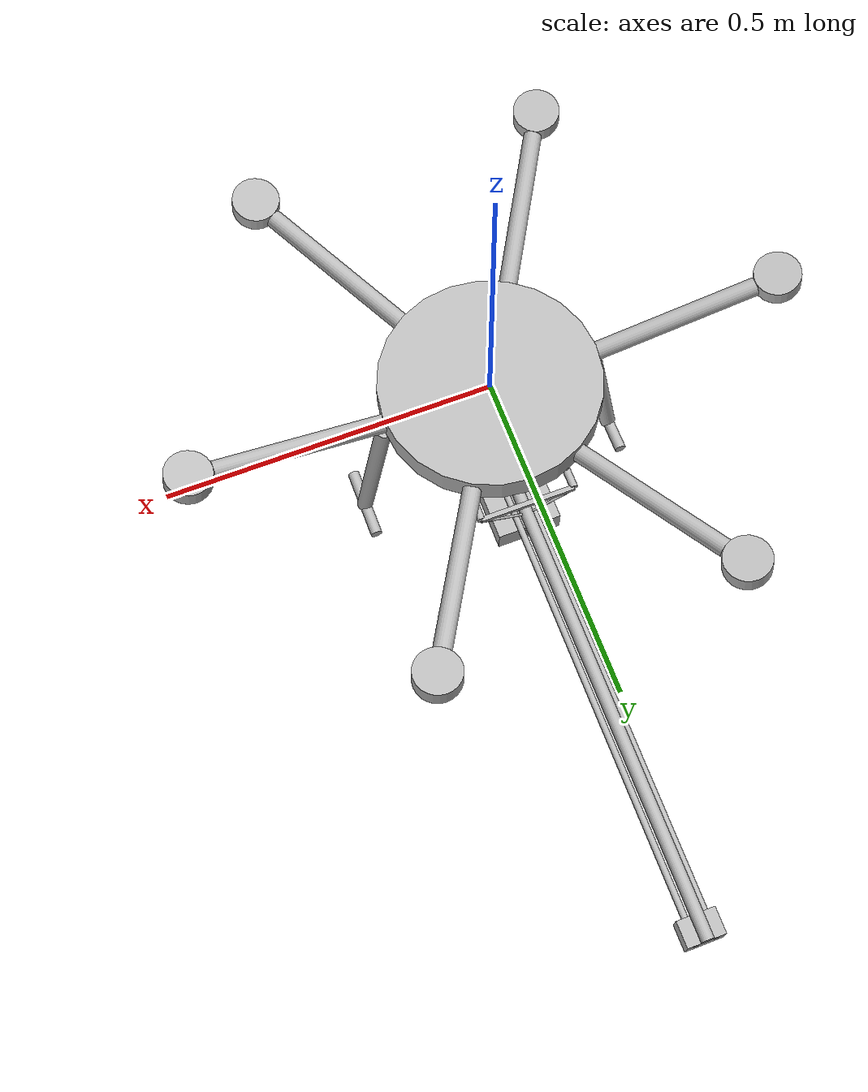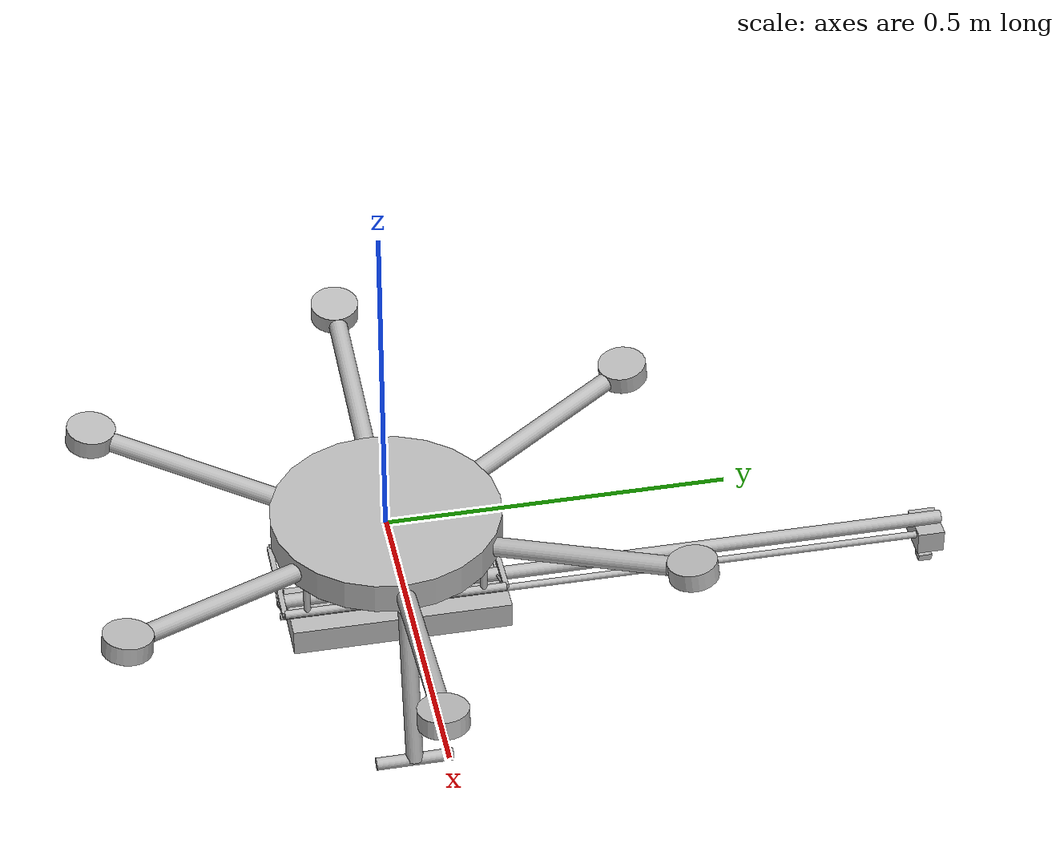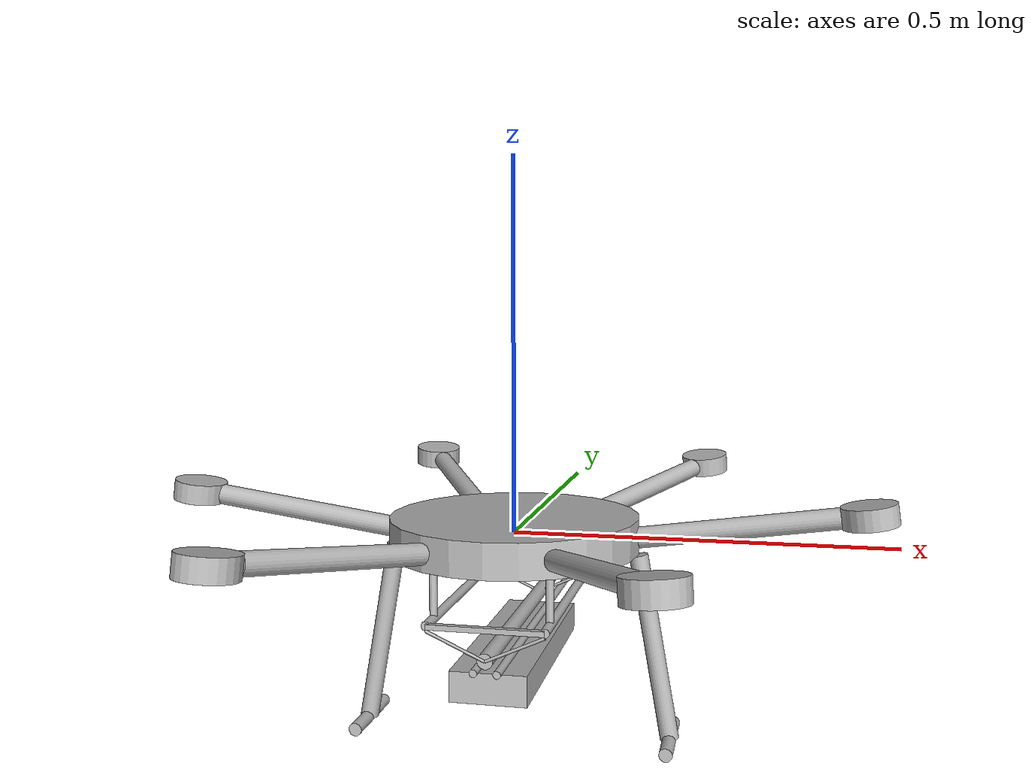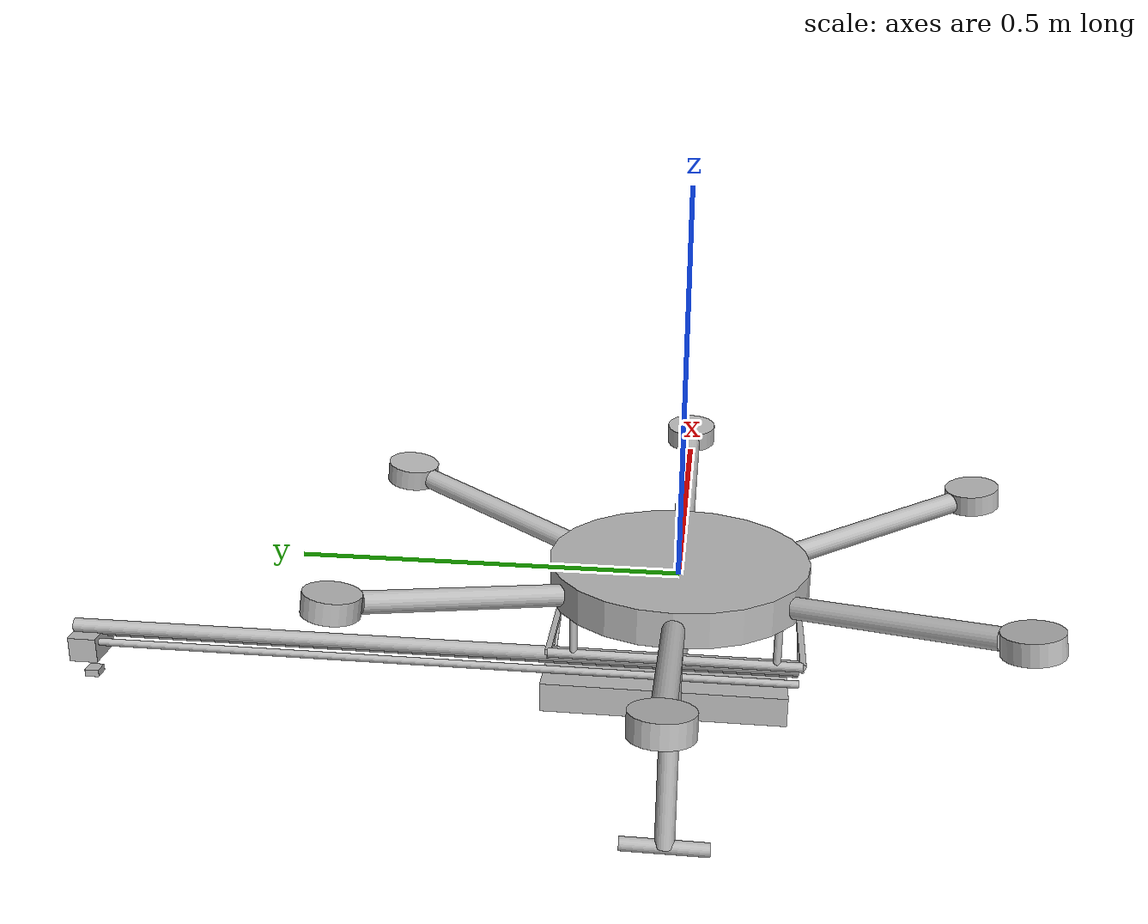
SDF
<?xml version='1.0'?>
<sdf version='1.6'>
		<model name="UAV">
			<self_collide>true</self_collide>
			<pose>0.0 0.0 0.0 0.0 0.0 0.0</pose>
			<!-- Start of parts of the pmodel UAV -->
				<!-- Start of declarations for part "UAV::drone" -->
					<!-- Start of parts of part "UAV::drone" -->
					<!-- Start of declarations for part "UAV::drone::LeftLeg" -->
						<!-- Start of parts of part "UAV::drone::LeftLeg" -->
						<!-- End of parts of part "UAV::drone::LeftLeg" -->

						<!-- Start of links of part "UAV::drone::LeftLeg" -->
						<!-- link full name is UAV::drone::LeftLeg::gear -->
						<link name="1-gear">
								<pose>0.16811999898880714 0.0 -0.023349999859556547 0.0 -0.17452777756585014 0.0</pose>
								<inertial>
									<pose>0.0 0.0 0.0 0.0 0.0 0.0</pose>
									<inertia>
										<ixx>1.0</ixx>
										<ixy>0.0</ixy>
										<ixz>0.0</ixz>
										<iyy>1.0</iyy>
										<iyz>0.0</iyz>
										<izz>1.0</izz>
									</inertia>
									<mass>1.0</mass>
								</inertial>
								<!-- body full name is UAV::drone::LeftLeg::gear::leg -->
								<collision name="1--leg">
									<laser_retro>0.0</laser_retro>
									<pose>0.0 0.0 -0.12654999450109905 0.0 -3.1414999961853027 0.0</pose>
									<geometry>
										<cylinder>
											<radius>0.012499999720603228</radius>
											<length>0.2530999890021981</length>
										</cylinder>
									</geometry>
									<surface>
										<bounce>
											<restitution_coefficient>0.0</restitution_coefficient>
											<threshold>100000.0</threshold>
										</bounce>
										<friction>
											<ode>
												<mu>1.0</mu>
												<mu2>1.0</mu2>
												<fdir1>0.0 0.0 0.0</fdir1>
												<slip1>0.0</slip1>
												<slip2>0.0</slip2>
											</ode>
											<torsional>
												<coefficient>1.0</coefficient>
												<surface_radius>0.0</surface_radius>
											</torsional>
										</friction>
									</surface>
								</collision>
								<visual name="1--leg">
									<laser_retro>0.0</laser_retro>
									<pose>0.0 0.0 -0.12654999450109905 0.0 -3.1414999961853027 0.0</pose>
									<geometry>
										<cylinder>
											<radius>0.012499999720603228</radius>
											<length>0.2530999890021981</length>
										</cylinder>
									</geometry>
									<surface>
										<bounce>
											<restitution_coefficient>0.0</restitution_coefficient>
											<threshold>100000.0</threshold>
										</bounce>
										<friction>
											<ode>
												<mu>1.0</mu>
												<mu2>1.0</mu2>
												<fdir1>0.0 0.0 0.0</fdir1>
												<slip1>0.0</slip1>
												<slip2>0.0</slip2>
											</ode>
											<torsional>
												<coefficient>1.0</coefficient>
												<surface_radius>0.0</surface_radius>
											</torsional>
										</friction>
									</surface>
								</visual>
								<!-- body full name is UAV::drone::LeftLeg::gear::foot -->
								<collision name="2--foot">
									<laser_retro>0.0</laser_retro>
									<pose>0.0 0.0 -0.2530999890021981 1.5707499980926514 -1.5707499980926514 0.0</pose>
									<geometry>
										<cylinder>
											<radius>0.00899999956041575</radius>
											<length>0.11249999748542905</length>
										</cylinder>
									</geometry>
									<surface>
										<bounce>
											<restitution_coefficient>0.0</restitution_coefficient>
											<threshold>100000.0</threshold>
										</bounce>
										<friction>
											<ode>
												<mu>1.0</mu>
												<mu2>1.0</mu2>
												<fdir1>0.0 0.0 0.0</fdir1>
												<slip1>0.0</slip1>
												<slip2>0.0</slip2>
											</ode>
											<torsional>
												<coefficient>1.0</coefficient>
												<surface_radius>0.0</surface_radius>
											</torsional>
										</friction>
									</surface>
								</collision>
								<visual name="2--foot">
									<laser_retro>0.0</laser_retro>
									<pose>0.0 0.0 -0.2530999890021981 1.5707499980926514 -1.5707499980926514 0.0</pose>
									<geometry>
										<cylinder>
											<radius>0.00899999956041575</radius>
											<length>0.11249999748542905</length>
										</cylinder>
									</geometry>
									<surface>
										<bounce>
											<restitution_coefficient>0.0</restitution_coefficient>
											<threshold>100000.0</threshold>
										</bounce>
										<friction>
											<ode>
												<mu>1.0</mu>
												<mu2>1.0</mu2>
												<fdir1>0.0 0.0 0.0</fdir1>
												<slip1>0.0</slip1>
												<slip2>0.0</slip2>
											</ode>
											<torsional>
												<coefficient>1.0</coefficient>
												<surface_radius>0.0</surface_radius>
											</torsional>
										</friction>
									</surface>
								</visual>
						</link>
						<!-- End of links of part "UAV::drone::LeftLeg" -->

						<!-- Start of joints of part "UAV::drone::LeftLeg" -->
						<!-- End of joints of part "UAV::drone::LeftLeg" -->

						<!-- Start of fixed connections of part "UAV::drone::LeftLeg" -->
						<!-- fixed joint full name is UAV::drone::LeftLeg::gear::fixedJoint::UAV::drone::Hub from UAV::drone::LeftLeg::gear to UAV::drone::Hub -->
						<joint name="3-fixedJoint" type="fixed">
							<parent>1-gear</parent>
							<child>2-Hub</child>
							<axis><xyz>0 0 1</xyz></axis>
						</joint>

						<!-- End of fixed connections of part "UAV::drone::LeftLeg" -->
					<!-- End of declarations for part "UAV::drone::LeftLeg" -->
					<!-- Start of declarations for part "UAV::drone::RightLeg" -->
						<!-- Start of parts of part "UAV::drone::RightLeg" -->
						<!-- End of parts of part "UAV::drone::RightLeg" -->

						<!-- Start of links of part "UAV::drone::RightLeg" -->
						<!-- link full name is UAV::drone::RightLeg::gear -->
						<link name="4-gear">
								<pose>-0.16811999898880714 0.0 -0.023349999859556547 0.0 -0.17452777756585014 3.1414999961853027</pose>
								<inertial>
									<pose>0.0 0.0 0.0 0.0 0.0 0.0</pose>
									<inertia>
										<ixx>1.0</ixx>
										<ixy>0.0</ixy>
										<ixz>0.0</ixz>
										<iyy>1.0</iyy>
										<iyz>0.0</iyz>
										<izz>1.0</izz>
									</inertia>
									<mass>1.0</mass>
								</inertial>
								<!-- body full name is UAV::drone::RightLeg::gear::leg -->
								<collision name="3--leg">
									<laser_retro>0.0</laser_retro>
									<pose>0.0 0.0 -0.12654999450109905 0.0 -3.1414999961853027 0.0</pose>
									<geometry>
										<cylinder>
											<radius>0.012499999720603228</radius>
											<length>0.2530999890021981</length>
										</cylinder>
									</geometry>
									<surface>
										<bounce>
											<restitution_coefficient>0.0</restitution_coefficient>
											<threshold>100000.0</threshold>
										</bounce>
										<friction>
											<ode>
												<mu>1.0</mu>
												<mu2>1.0</mu2>
												<fdir1>0.0 0.0 0.0</fdir1>
												<slip1>0.0</slip1>
												<slip2>0.0</slip2>
											</ode>
											<torsional>
												<coefficient>1.0</coefficient>
												<surface_radius>0.0</surface_radius>
											</torsional>
										</friction>
									</surface>
								</collision>
								<visual name="3--leg">
									<laser_retro>0.0</laser_retro>
									<pose>0.0 0.0 -0.12654999450109905 0.0 -3.1414999961853027 0.0</pose>
									<geometry>
										<cylinder>
											<radius>0.012499999720603228</radius>
											<length>0.2530999890021981</length>
										</cylinder>
									</geometry>
									<surface>
										<bounce>
											<restitution_coefficient>0.0</restitution_coefficient>
											<threshold>100000.0</threshold>
										</bounce>
										<friction>
											<ode>
												<mu>1.0</mu>
												<mu2>1.0</mu2>
												<fdir1>0.0 0.0 0.0</fdir1>
												<slip1>0.0</slip1>
												<slip2>0.0</slip2>
											</ode>
											<torsional>
												<coefficient>1.0</coefficient>
												<surface_radius>0.0</surface_radius>
											</torsional>
										</friction>
									</surface>
								</visual>
								<!-- body full name is UAV::drone::RightLeg::gear::foot -->
								<collision name="4--foot">
									<laser_retro>0.0</laser_retro>
									<pose>0.0 0.0 -0.2530999890021981 1.5707499980926514 -1.5707499980926514 0.0</pose>
									<geometry>
										<cylinder>
											<radius>0.00899999956041575</radius>
											<length>0.11249999748542905</length>
										</cylinder>
									</geometry>
									<surface>
										<bounce>
											<restitution_coefficient>0.0</restitution_coefficient>
											<threshold>100000.0</threshold>
										</bounce>
										<friction>
											<ode>
												<mu>1.0</mu>
												<mu2>1.0</mu2>
												<fdir1>0.0 0.0 0.0</fdir1>
												<slip1>0.0</slip1>
												<slip2>0.0</slip2>
											</ode>
											<torsional>
												<coefficient>1.0</coefficient>
												<surface_radius>0.0</surface_radius>
											</torsional>
										</friction>
									</surface>
								</collision>
								<visual name="4--foot">
									<laser_retro>0.0</laser_retro>
									<pose>0.0 0.0 -0.2530999890021981 1.5707499980926514 -1.5707499980926514 0.0</pose>
									<geometry>
										<cylinder>
											<radius>0.00899999956041575</radius>
											<length>0.11249999748542905</length>
										</cylinder>
									</geometry>
									<surface>
										<bounce>
											<restitution_coefficient>0.0</restitution_coefficient>
											<threshold>100000.0</threshold>
										</bounce>
										<friction>
											<ode>
												<mu>1.0</mu>
												<mu2>1.0</mu2>
												<fdir1>0.0 0.0 0.0</fdir1>
												<slip1>0.0</slip1>
												<slip2>0.0</slip2>
											</ode>
											<torsional>
												<coefficient>1.0</coefficient>
												<surface_radius>0.0</surface_radius>
											</torsional>
										</friction>
									</surface>
								</visual>
						</link>
						<!-- End of links of part "UAV::drone::RightLeg" -->

						<!-- Start of joints of part "UAV::drone::RightLeg" -->
						<!-- End of joints of part "UAV::drone::RightLeg" -->

						<!-- Start of fixed connections of part "UAV::drone::RightLeg" -->
						<!-- fixed joint full name is UAV::drone::RightLeg::gear::fixedJoint::UAV::drone::Hub from UAV::drone::RightLeg::gear to UAV::drone::Hub -->
						<joint name="5-fixedJoint" type="fixed">
							<parent>4-gear</parent>
							<child>2-Hub</child>
							<axis><xyz>0 0 1</xyz></axis>
						</joint>

						<!-- End of fixed connections of part "UAV::drone::RightLeg" -->
					<!-- End of declarations for part "UAV::drone::RightLeg" -->
					<!-- Start of declarations for part "UAV::drone::arm::1" -->
						<!-- Start of parts of part "UAV::drone::arm::1" -->
						<!-- End of parts of part "UAV::drone::arm::1" -->

						<!-- Start of links of part "UAV::drone::arm::1" -->
						<!-- link full name is UAV::drone::arm::1::arm -->
						<link name="6-arm">
								<pose>0.08406449630933237 0.14559359367861882 0.0 0.0 -0.1396222220526801 1.0471666653951008</pose>
								<inertial>
									<pose>0.0 0.0 0.0 0.0 0.0 0.0</pose>
									<inertia>
										<ixx>1.0</ixx>
										<ixy>0.0</ixy>
										<ixz>0.0</ixz>
										<iyy>1.0</iyy>
										<iyz>0.0</iyz>
										<izz>1.0</izz>
									</inertia>
									<mass>1.0</mass>
								</inertial>
								<!-- body full name is UAV::drone::arm::1::arm::Pole -->
								<collision name="5--Pole">
									<laser_retro>0.0</laser_retro>
									<pose>0.129949995950982 0.0 0.0 0.0 -1.5707499980926514 0.0</pose>
									<geometry>
										<cylinder>
											<radius>0.013999999448657041</radius>
											<length>0.259899991901964</length>
										</cylinder>
									</geometry>
									<surface>
										<bounce>
											<restitution_coefficient>0.0</restitution_coefficient>
											<threshold>100000.0</threshold>
										</bounce>
										<friction>
											<ode>
												<mu>1.0</mu>
												<mu2>1.0</mu2>
												<fdir1>0.0 0.0 0.0</fdir1>
												<slip1>0.0</slip1>
												<slip2>0.0</slip2>
											</ode>
											<torsional>
												<coefficient>1.0</coefficient>
												<surface_radius>0.0</surface_radius>
											</torsional>
										</friction>
									</surface>
								</collision>
								<visual name="5--Pole">
									<laser_retro>0.0</laser_retro>
									<pose>0.129949995950982 0.0 0.0 0.0 -1.5707499980926514 0.0</pose>
									<geometry>
										<cylinder>
											<radius>0.013999999448657041</radius>
											<length>0.259899991901964</length>
										</cylinder>
									</geometry>
									<surface>
										<bounce>
											<restitution_coefficient>0.0</restitution_coefficient>
											<threshold>100000.0</threshold>
										</bounce>
										<friction>
											<ode>
												<mu>1.0</mu>
												<mu2>1.0</mu2>
												<fdir1>0.0 0.0 0.0</fdir1>
												<slip1>0.0</slip1>
												<slip2>0.0</slip2>
											</ode>
											<torsional>
												<coefficient>1.0</coefficient>
												<surface_radius>0.0</surface_radius>
											</torsional>
										</friction>
									</surface>
								</visual>
								<!-- body full name is UAV::drone::arm::1::arm::MotorHolder -->
								<collision name="6--MotorHolder">
									<laser_retro>0.0</laser_retro>
									<pose>0.295899990143627 0.0 0.0 0.0 0.0 0.0</pose>
									<geometry>
										<cylinder>
											<radius>0.035999998241663</radius>
											<length>0.027999998897314082</length>
										</cylinder>
									</geometry>
									<surface>
										<bounce>
											<restitution_coefficient>0.0</restitution_coefficient>
											<threshold>100000.0</threshold>
										</bounce>
										<friction>
											<ode>
												<mu>1.0</mu>
												<mu2>1.0</mu2>
												<fdir1>0.0 0.0 0.0</fdir1>
												<slip1>0.0</slip1>
												<slip2>0.0</slip2>
											</ode>
											<torsional>
												<coefficient>1.0</coefficient>
												<surface_radius>0.0</surface_radius>
											</torsional>
										</friction>
									</surface>
								</collision>
								<visual name="6--MotorHolder">
									<laser_retro>0.0</laser_retro>
									<pose>0.295899990143627 0.0 0.0 0.0 0.0 0.0</pose>
									<geometry>
										<cylinder>
											<radius>0.035999998241663</radius>
											<length>0.027999998897314082</length>
										</cylinder>
									</geometry>
									<surface>
										<bounce>
											<restitution_coefficient>0.0</restitution_coefficient>
											<threshold>100000.0</threshold>
										</bounce>
										<friction>
											<ode>
												<mu>1.0</mu>
												<mu2>1.0</mu2>
												<fdir1>0.0 0.0 0.0</fdir1>
												<slip1>0.0</slip1>
												<slip2>0.0</slip2>
											</ode>
											<torsional>
												<coefficient>1.0</coefficient>
												<surface_radius>0.0</surface_radius>
											</torsional>
										</friction>
									</surface>
								</visual>
						</link>
						<!-- End of links of part "UAV::drone::arm::1" -->

						<!-- Start of joints of part "UAV::drone::arm::1" -->
						<!-- End of joints of part "UAV::drone::arm::1" -->

						<!-- Start of fixed connections of part "UAV::drone::arm::1" -->

						<!-- End of fixed connections of part "UAV::drone::arm::1" -->
					<!-- End of declarations for part "UAV::drone::arm::1" -->
					<!-- Start of declarations for part "UAV::drone::arm::2" -->
						<!-- Start of parts of part "UAV::drone::arm::2" -->
						<!-- End of parts of part "UAV::drone::arm::2" -->

						<!-- Start of links of part "UAV::drone::arm::2" -->
						<!-- link full name is UAV::drone::arm::2::arm -->
						<link name="7-arm">
								<pose>-0.0840510056239875 0.1456013822516563 0.0 0.0 -0.1396222220526801 2.094333330790202</pose>
								<inertial>
									<pose>0.0 0.0 0.0 0.0 0.0 0.0</pose>
									<inertia>
										<ixx>1.0</ixx>
										<ixy>0.0</ixy>
										<ixz>0.0</ixz>
										<iyy>1.0</iyy>
										<iyz>0.0</iyz>
										<izz>1.0</izz>
									</inertia>
									<mass>1.0</mass>
								</inertial>
								<!-- body full name is UAV::drone::arm::2::arm::Pole -->
								<collision name="7--Pole">
									<laser_retro>0.0</laser_retro>
									<pose>0.129949995950982 0.0 0.0 0.0 -1.5707499980926514 0.0</pose>
									<geometry>
										<cylinder>
											<radius>0.013999999448657041</radius>
											<length>0.259899991901964</length>
										</cylinder>
									</geometry>
									<surface>
										<bounce>
											<restitution_coefficient>0.0</restitution_coefficient>
											<threshold>100000.0</threshold>
										</bounce>
										<friction>
											<ode>
												<mu>1.0</mu>
												<mu2>1.0</mu2>
												<fdir1>0.0 0.0 0.0</fdir1>
												<slip1>0.0</slip1>
												<slip2>0.0</slip2>
											</ode>
											<torsional>
												<coefficient>1.0</coefficient>
												<surface_radius>0.0</surface_radius>
											</torsional>
										</friction>
									</surface>
								</collision>
								<visual name="7--Pole">
									<laser_retro>0.0</laser_retro>
									<pose>0.129949995950982 0.0 0.0 0.0 -1.5707499980926514 0.0</pose>
									<geometry>
										<cylinder>
											<radius>0.013999999448657041</radius>
											<length>0.259899991901964</length>
										</cylinder>
									</geometry>
									<surface>
										<bounce>
											<restitution_coefficient>0.0</restitution_coefficient>
											<threshold>100000.0</threshold>
										</bounce>
										<friction>
											<ode>
												<mu>1.0</mu>
												<mu2>1.0</mu2>
												<fdir1>0.0 0.0 0.0</fdir1>
												<slip1>0.0</slip1>
												<slip2>0.0</slip2>
											</ode>
											<torsional>
												<coefficient>1.0</coefficient>
												<surface_radius>0.0</surface_radius>
											</torsional>
										</friction>
									</surface>
								</visual>
								<!-- body full name is UAV::drone::arm::2::arm::MotorHolder -->
								<collision name="8--MotorHolder">
									<laser_retro>0.0</laser_retro>
									<pose>0.295899990143627 0.0 0.0 0.0 0.0 0.0</pose>
									<geometry>
										<cylinder>
											<radius>0.035999998241663</radius>
											<length>0.027999998897314082</length>
										</cylinder>
									</geometry>
									<surface>
										<bounce>
											<restitution_coefficient>0.0</restitution_coefficient>
											<threshold>100000.0</threshold>
										</bounce>
										<friction>
											<ode>
												<mu>1.0</mu>
												<mu2>1.0</mu2>
												<fdir1>0.0 0.0 0.0</fdir1>
												<slip1>0.0</slip1>
												<slip2>0.0</slip2>
											</ode>
											<torsional>
												<coefficient>1.0</coefficient>
												<surface_radius>0.0</surface_radius>
											</torsional>
										</friction>
									</surface>
								</collision>
								<visual name="8--MotorHolder">
									<laser_retro>0.0</laser_retro>
									<pose>0.295899990143627 0.0 0.0 0.0 0.0 0.0</pose>
									<geometry>
										<cylinder>
											<radius>0.035999998241663</radius>
											<length>0.027999998897314082</length>
										</cylinder>
									</geometry>
									<surface>
										<bounce>
											<restitution_coefficient>0.0</restitution_coefficient>
											<threshold>100000.0</threshold>
										</bounce>
										<friction>
											<ode>
												<mu>1.0</mu>
												<mu2>1.0</mu2>
												<fdir1>0.0 0.0 0.0</fdir1>
												<slip1>0.0</slip1>
												<slip2>0.0</slip2>
											</ode>
											<torsional>
												<coefficient>1.0</coefficient>
												<surface_radius>0.0</surface_radius>
											</torsional>
										</friction>
									</surface>
								</visual>
						</link>
						<!-- End of links of part "UAV::drone::arm::2" -->

						<!-- Start of joints of part "UAV::drone::arm::2" -->
						<!-- End of joints of part "UAV::drone::arm::2" -->

						<!-- Start of fixed connections of part "UAV::drone::arm::2" -->

						<!-- End of fixed connections of part "UAV::drone::arm::2" -->
					<!-- End of declarations for part "UAV::drone::arm::2" -->
					<!-- Start of declarations for part "UAV::drone::arm::3" -->
						<!-- Start of parts of part "UAV::drone::arm::3" -->
						<!-- End of parts of part "UAV::drone::arm::3" -->

						<!-- Start of links of part "UAV::drone::arm::3" -->
						<!-- link full name is UAV::drone::arm::3::arm -->
						<link name="8-arm">
								<pose>-0.16811999826711888 1.557756272695912E-5 0.0 0.0 -0.1396222220526801 3.1414999961853027</pose>
								<inertial>
									<pose>0.0 0.0 0.0 0.0 0.0 0.0</pose>
									<inertia>
										<ixx>1.0</ixx>
										<ixy>0.0</ixy>
										<ixz>0.0</ixz>
										<iyy>1.0</iyy>
										<iyz>0.0</iyz>
										<izz>1.0</izz>
									</inertia>
									<mass>1.0</mass>
								</inertial>
								<!-- body full name is UAV::drone::arm::3::arm::Pole -->
								<collision name="9--Pole">
									<laser_retro>0.0</laser_retro>
									<pose>0.129949995950982 0.0 0.0 0.0 -1.5707499980926514 0.0</pose>
									<geometry>
										<cylinder>
											<radius>0.013999999448657041</radius>
											<length>0.259899991901964</length>
										</cylinder>
									</geometry>
									<surface>
										<bounce>
											<restitution_coefficient>0.0</restitution_coefficient>
											<threshold>100000.0</threshold>
										</bounce>
										<friction>
											<ode>
												<mu>1.0</mu>
												<mu2>1.0</mu2>
												<fdir1>0.0 0.0 0.0</fdir1>
												<slip1>0.0</slip1>
												<slip2>0.0</slip2>
											</ode>
											<torsional>
												<coefficient>1.0</coefficient>
												<surface_radius>0.0</surface_radius>
											</torsional>
										</friction>
									</surface>
								</collision>
								<visual name="9--Pole">
									<laser_retro>0.0</laser_retro>
									<pose>0.129949995950982 0.0 0.0 0.0 -1.5707499980926514 0.0</pose>
									<geometry>
										<cylinder>
											<radius>0.013999999448657041</radius>
											<length>0.259899991901964</length>
										</cylinder>
									</geometry>
									<surface>
										<bounce>
											<restitution_coefficient>0.0</restitution_coefficient>
											<threshold>100000.0</threshold>
										</bounce>
										<friction>
											<ode>
												<mu>1.0</mu>
												<mu2>1.0</mu2>
												<fdir1>0.0 0.0 0.0</fdir1>
												<slip1>0.0</slip1>
												<slip2>0.0</slip2>
											</ode>
											<torsional>
												<coefficient>1.0</coefficient>
												<surface_radius>0.0</surface_radius>
											</torsional>
										</friction>
									</surface>
								</visual>
								<!-- body full name is UAV::drone::arm::3::arm::MotorHolder -->
								<collision name="10--MotorHolder">
									<laser_retro>0.0</laser_retro>
									<pose>0.295899990143627 0.0 0.0 0.0 0.0 0.0</pose>
									<geometry>
										<cylinder>
											<radius>0.035999998241663</radius>
											<length>0.027999998897314082</length>
										</cylinder>
									</geometry>
									<surface>
										<bounce>
											<restitution_coefficient>0.0</restitution_coefficient>
											<threshold>100000.0</threshold>
										</bounce>
										<friction>
											<ode>
												<mu>1.0</mu>
												<mu2>1.0</mu2>
												<fdir1>0.0 0.0 0.0</fdir1>
												<slip1>0.0</slip1>
												<slip2>0.0</slip2>
											</ode>
											<torsional>
												<coefficient>1.0</coefficient>
												<surface_radius>0.0</surface_radius>
											</torsional>
										</friction>
									</surface>
								</collision>
								<visual name="10--MotorHolder">
									<laser_retro>0.0</laser_retro>
									<pose>0.295899990143627 0.0 0.0 0.0 0.0 0.0</pose>
									<geometry>
										<cylinder>
											<radius>0.035999998241663</radius>
											<length>0.027999998897314082</length>
										</cylinder>
									</geometry>
									<surface>
										<bounce>
											<restitution_coefficient>0.0</restitution_coefficient>
											<threshold>100000.0</threshold>
										</bounce>
										<friction>
											<ode>
												<mu>1.0</mu>
												<mu2>1.0</mu2>
												<fdir1>0.0 0.0 0.0</fdir1>
												<slip1>0.0</slip1>
												<slip2>0.0</slip2>
											</ode>
											<torsional>
												<coefficient>1.0</coefficient>
												<surface_radius>0.0</surface_radius>
											</torsional>
										</friction>
									</surface>
								</visual>
						</link>
						<!-- End of links of part "UAV::drone::arm::3" -->

						<!-- Start of joints of part "UAV::drone::arm::3" -->
						<!-- End of joints of part "UAV::drone::arm::3" -->

						<!-- Start of fixed connections of part "UAV::drone::arm::3" -->

						<!-- End of fixed connections of part "UAV::drone::arm::3" -->
					<!-- End of declarations for part "UAV::drone::arm::3" -->
					<!-- Start of declarations for part "UAV::drone::arm::4" -->
						<!-- Start of parts of part "UAV::drone::arm::4" -->
						<!-- End of parts of part "UAV::drone::arm::4" -->

						<!-- Start of links of part "UAV::drone::arm::4" -->
						<!-- link full name is UAV::drone::arm::4::arm -->
						<link name="9-arm">
								<pose>-0.08407798627295038 -0.1455858038556029 0.0 0.0 -0.1396222220526801 -2.0945186455991833</pose>
								<inertial>
									<pose>0.0 0.0 0.0 0.0 0.0 0.0</pose>
									<inertia>
										<ixx>1.0</ixx>
										<ixy>0.0</ixy>
										<ixz>0.0</ixz>
										<iyy>1.0</iyy>
										<iyz>0.0</iyz>
										<izz>1.0</izz>
									</inertia>
									<mass>1.0</mass>
								</inertial>
								<!-- body full name is UAV::drone::arm::4::arm::Pole -->
								<collision name="11--Pole">
									<laser_retro>0.0</laser_retro>
									<pose>0.129949995950982 0.0 0.0 0.0 -1.5707499980926514 0.0</pose>
									<geometry>
										<cylinder>
											<radius>0.013999999448657041</radius>
											<length>0.259899991901964</length>
										</cylinder>
									</geometry>
									<surface>
										<bounce>
											<restitution_coefficient>0.0</restitution_coefficient>
											<threshold>100000.0</threshold>
										</bounce>
										<friction>
											<ode>
												<mu>1.0</mu>
												<mu2>1.0</mu2>
												<fdir1>0.0 0.0 0.0</fdir1>
												<slip1>0.0</slip1>
												<slip2>0.0</slip2>
											</ode>
											<torsional>
												<coefficient>1.0</coefficient>
												<surface_radius>0.0</surface_radius>
											</torsional>
										</friction>
									</surface>
								</collision>
								<visual name="11--Pole">
									<laser_retro>0.0</laser_retro>
									<pose>0.129949995950982 0.0 0.0 0.0 -1.5707499980926514 0.0</pose>
									<geometry>
										<cylinder>
											<radius>0.013999999448657041</radius>
											<length>0.259899991901964</length>
										</cylinder>
									</geometry>
									<surface>
										<bounce>
											<restitution_coefficient>0.0</restitution_coefficient>
											<threshold>100000.0</threshold>
										</bounce>
										<friction>
											<ode>
												<mu>1.0</mu>
												<mu2>1.0</mu2>
												<fdir1>0.0 0.0 0.0</fdir1>
												<slip1>0.0</slip1>
												<slip2>0.0</slip2>
											</ode>
											<torsional>
												<coefficient>1.0</coefficient>
												<surface_radius>0.0</surface_radius>
											</torsional>
										</friction>
									</surface>
								</visual>
								<!-- body full name is UAV::drone::arm::4::arm::MotorHolder -->
								<collision name="12--MotorHolder">
									<laser_retro>0.0</laser_retro>
									<pose>0.295899990143627 0.0 0.0 0.0 0.0 0.0</pose>
									<geometry>
										<cylinder>
											<radius>0.035999998241663</radius>
											<length>0.027999998897314082</length>
										</cylinder>
									</geometry>
									<surface>
										<bounce>
											<restitution_coefficient>0.0</restitution_coefficient>
											<threshold>100000.0</threshold>
										</bounce>
										<friction>
											<ode>
												<mu>1.0</mu>
												<mu2>1.0</mu2>
												<fdir1>0.0 0.0 0.0</fdir1>
												<slip1>0.0</slip1>
												<slip2>0.0</slip2>
											</ode>
											<torsional>
												<coefficient>1.0</coefficient>
												<surface_radius>0.0</surface_radius>
											</torsional>
										</friction>
									</surface>
								</collision>
								<visual name="12--MotorHolder">
									<laser_retro>0.0</laser_retro>
									<pose>0.295899990143627 0.0 0.0 0.0 0.0 0.0</pose>
									<geometry>
										<cylinder>
											<radius>0.035999998241663</radius>
											<length>0.027999998897314082</length>
										</cylinder>
									</geometry>
									<surface>
										<bounce>
											<restitution_coefficient>0.0</restitution_coefficient>
											<threshold>100000.0</threshold>
										</bounce>
										<friction>
											<ode>
												<mu>1.0</mu>
												<mu2>1.0</mu2>
												<fdir1>0.0 0.0 0.0</fdir1>
												<slip1>0.0</slip1>
												<slip2>0.0</slip2>
											</ode>
											<torsional>
												<coefficient>1.0</coefficient>
												<surface_radius>0.0</surface_radius>
											</torsional>
										</friction>
									</surface>
								</visual>
						</link>
						<!-- End of links of part "UAV::drone::arm::4" -->

						<!-- Start of joints of part "UAV::drone::arm::4" -->
						<!-- End of joints of part "UAV::drone::arm::4" -->

						<!-- Start of fixed connections of part "UAV::drone::arm::4" -->

						<!-- End of fixed connections of part "UAV::drone::arm::4" -->
					<!-- End of declarations for part "UAV::drone::arm::4" -->
					<!-- Start of declarations for part "UAV::drone::arm::5" -->
						<!-- Start of parts of part "UAV::drone::arm::5" -->
						<!-- End of parts of part "UAV::drone::arm::5" -->

						<!-- Start of links of part "UAV::drone::arm::5" -->
						<!-- link full name is UAV::drone::arm::5::arm -->
						<link name="10-arm">
								<pose>0.08403751421703155 -0.14560916957464848 0.0 0.0 -0.1396222220526801 -1.0473519802040825</pose>
								<inertial>
									<pose>0.0 0.0 0.0 0.0 0.0 0.0</pose>
									<inertia>
										<ixx>1.0</ixx>
										<ixy>0.0</ixy>
										<ixz>0.0</ixz>
										<iyy>1.0</iyy>
										<iyz>0.0</iyz>
										<izz>1.0</izz>
									</inertia>
									<mass>1.0</mass>
								</inertial>
								<!-- body full name is UAV::drone::arm::5::arm::Pole -->
								<collision name="13--Pole">
									<laser_retro>0.0</laser_retro>
									<pose>0.129949995950982 0.0 0.0 0.0 -1.5707499980926514 0.0</pose>
									<geometry>
										<cylinder>
											<radius>0.013999999448657041</radius>
											<length>0.259899991901964</length>
										</cylinder>
									</geometry>
									<surface>
										<bounce>
											<restitution_coefficient>0.0</restitution_coefficient>
											<threshold>100000.0</threshold>
										</bounce>
										<friction>
											<ode>
												<mu>1.0</mu>
												<mu2>1.0</mu2>
												<fdir1>0.0 0.0 0.0</fdir1>
												<slip1>0.0</slip1>
												<slip2>0.0</slip2>
											</ode>
											<torsional>
												<coefficient>1.0</coefficient>
												<surface_radius>0.0</surface_radius>
											</torsional>
										</friction>
									</surface>
								</collision>
								<visual name="13--Pole">
									<laser_retro>0.0</laser_retro>
									<pose>0.129949995950982 0.0 0.0 0.0 -1.5707499980926514 0.0</pose>
									<geometry>
										<cylinder>
											<radius>0.013999999448657041</radius>
											<length>0.259899991901964</length>
										</cylinder>
									</geometry>
									<surface>
										<bounce>
											<restitution_coefficient>0.0</restitution_coefficient>
											<threshold>100000.0</threshold>
										</bounce>
										<friction>
											<ode>
												<mu>1.0</mu>
												<mu2>1.0</mu2>
												<fdir1>0.0 0.0 0.0</fdir1>
												<slip1>0.0</slip1>
												<slip2>0.0</slip2>
											</ode>
											<torsional>
												<coefficient>1.0</coefficient>
												<surface_radius>0.0</surface_radius>
											</torsional>
										</friction>
									</surface>
								</visual>
								<!-- body full name is UAV::drone::arm::5::arm::MotorHolder -->
								<collision name="14--MotorHolder">
									<laser_retro>0.0</laser_retro>
									<pose>0.295899990143627 0.0 0.0 0.0 0.0 0.0</pose>
									<geometry>
										<cylinder>
											<radius>0.035999998241663</radius>
											<length>0.027999998897314082</length>
										</cylinder>
									</geometry>
									<surface>
										<bounce>
											<restitution_coefficient>0.0</restitution_coefficient>
											<threshold>100000.0</threshold>
										</bounce>
										<friction>
											<ode>
												<mu>1.0</mu>
												<mu2>1.0</mu2>
												<fdir1>0.0 0.0 0.0</fdir1>
												<slip1>0.0</slip1>
												<slip2>0.0</slip2>
											</ode>
											<torsional>
												<coefficient>1.0</coefficient>
												<surface_radius>0.0</surface_radius>
											</torsional>
										</friction>
									</surface>
								</collision>
								<visual name="14--MotorHolder">
									<laser_retro>0.0</laser_retro>
									<pose>0.295899990143627 0.0 0.0 0.0 0.0 0.0</pose>
									<geometry>
										<cylinder>
											<radius>0.035999998241663</radius>
											<length>0.027999998897314082</length>
										</cylinder>
									</geometry>
									<surface>
										<bounce>
											<restitution_coefficient>0.0</restitution_coefficient>
											<threshold>100000.0</threshold>
										</bounce>
										<friction>
											<ode>
												<mu>1.0</mu>
												<mu2>1.0</mu2>
												<fdir1>0.0 0.0 0.0</fdir1>
												<slip1>0.0</slip1>
												<slip2>0.0</slip2>
											</ode>
											<torsional>
												<coefficient>1.0</coefficient>
												<surface_radius>0.0</surface_radius>
											</torsional>
										</friction>
									</surface>
								</visual>
						</link>
						<!-- End of links of part "UAV::drone::arm::5" -->

						<!-- Start of joints of part "UAV::drone::arm::5" -->
						<!-- End of joints of part "UAV::drone::arm::5" -->

						<!-- Start of fixed connections of part "UAV::drone::arm::5" -->

						<!-- End of fixed connections of part "UAV::drone::arm::5" -->
					<!-- End of declarations for part "UAV::drone::arm::5" -->
					<!-- Start of declarations for part "UAV::drone::arm::6" -->
						<!-- Start of parts of part "UAV::drone::arm::6" -->
						<!-- End of parts of part "UAV::drone::arm::6" -->

						<!-- Start of links of part "UAV::drone::arm::6" -->
						<!-- link full name is UAV::drone::arm::6::arm -->
						<link name="11-arm">
								<pose>0.16811999610205408 -3.115512532017872E-5 0.0 0.0 -0.1396222220526801 -1.8531480898100817E-4</pose>
								<inertial>
									<pose>0.0 0.0 0.0 0.0 0.0 0.0</pose>
									<inertia>
										<ixx>1.0</ixx>
										<ixy>0.0</ixy>
										<ixz>0.0</ixz>
										<iyy>1.0</iyy>
										<iyz>0.0</iyz>
										<izz>1.0</izz>
									</inertia>
									<mass>1.0</mass>
								</inertial>
								<!-- body full name is UAV::drone::arm::6::arm::Pole -->
								<collision name="15--Pole">
									<laser_retro>0.0</laser_retro>
									<pose>0.129949995950982 0.0 0.0 0.0 -1.5707499980926514 0.0</pose>
									<geometry>
										<cylinder>
											<radius>0.013999999448657041</radius>
											<length>0.259899991901964</length>
										</cylinder>
									</geometry>
									<surface>
										<bounce>
											<restitution_coefficient>0.0</restitution_coefficient>
											<threshold>100000.0</threshold>
										</bounce>
										<friction>
											<ode>
												<mu>1.0</mu>
												<mu2>1.0</mu2>
												<fdir1>0.0 0.0 0.0</fdir1>
												<slip1>0.0</slip1>
												<slip2>0.0</slip2>
											</ode>
											<torsional>
												<coefficient>1.0</coefficient>
												<surface_radius>0.0</surface_radius>
											</torsional>
										</friction>
									</surface>
								</collision>
								<visual name="15--Pole">
									<laser_retro>0.0</laser_retro>
									<pose>0.129949995950982 0.0 0.0 0.0 -1.5707499980926514 0.0</pose>
									<geometry>
										<cylinder>
											<radius>0.013999999448657041</radius>
											<length>0.259899991901964</length>
										</cylinder>
									</geometry>
									<surface>
										<bounce>
											<restitution_coefficient>0.0</restitution_coefficient>
											<threshold>100000.0</threshold>
										</bounce>
										<friction>
											<ode>
												<mu>1.0</mu>
												<mu2>1.0</mu2>
												<fdir1>0.0 0.0 0.0</fdir1>
												<slip1>0.0</slip1>
												<slip2>0.0</slip2>
											</ode>
											<torsional>
												<coefficient>1.0</coefficient>
												<surface_radius>0.0</surface_radius>
											</torsional>
										</friction>
									</surface>
								</visual>
								<!-- body full name is UAV::drone::arm::6::arm::MotorHolder -->
								<collision name="16--MotorHolder">
									<laser_retro>0.0</laser_retro>
									<pose>0.295899990143627 0.0 0.0 0.0 0.0 0.0</pose>
									<geometry>
										<cylinder>
											<radius>0.035999998241663</radius>
											<length>0.027999998897314082</length>
										</cylinder>
									</geometry>
									<surface>
										<bounce>
											<restitution_coefficient>0.0</restitution_coefficient>
											<threshold>100000.0</threshold>
										</bounce>
										<friction>
											<ode>
												<mu>1.0</mu>
												<mu2>1.0</mu2>
												<fdir1>0.0 0.0 0.0</fdir1>
												<slip1>0.0</slip1>
												<slip2>0.0</slip2>
											</ode>
											<torsional>
												<coefficient>1.0</coefficient>
												<surface_radius>0.0</surface_radius>
											</torsional>
										</friction>
									</surface>
								</collision>
								<visual name="16--MotorHolder">
									<laser_retro>0.0</laser_retro>
									<pose>0.295899990143627 0.0 0.0 0.0 0.0 0.0</pose>
									<geometry>
										<cylinder>
											<radius>0.035999998241663</radius>
											<length>0.027999998897314082</length>
										</cylinder>
									</geometry>
									<surface>
										<bounce>
											<restitution_coefficient>0.0</restitution_coefficient>
											<threshold>100000.0</threshold>
										</bounce>
										<friction>
											<ode>
												<mu>1.0</mu>
												<mu2>1.0</mu2>
												<fdir1>0.0 0.0 0.0</fdir1>
												<slip1>0.0</slip1>
												<slip2>0.0</slip2>
											</ode>
											<torsional>
												<coefficient>1.0</coefficient>
												<surface_radius>0.0</surface_radius>
											</torsional>
										</friction>
									</surface>
								</visual>
						</link>
						<!-- End of links of part "UAV::drone::arm::6" -->

						<!-- Start of joints of part "UAV::drone::arm::6" -->
						<!-- End of joints of part "UAV::drone::arm::6" -->

						<!-- Start of fixed connections of part "UAV::drone::arm::6" -->

						<!-- End of fixed connections of part "UAV::drone::arm::6" -->
					<!-- End of declarations for part "UAV::drone::arm::6" -->
					<!-- End of parts of part "UAV::drone" -->

					<!-- Start of links of part "UAV::drone" -->
					<!-- link full name is UAV::drone::Hub -->
					<link name="2-Hub">
							<pose>0.0 0.0 0.0 0.0 0.0 0.0</pose>
							<inertial>
								<pose>0.0 0.0 0.0 0.0 0.0 0.0</pose>
								<inertia>
									<ixx>1.0</ixx>
									<ixy>0.0</ixy>
									<ixz>0.0</ixz>
									<iyy>1.0</iyy>
									<iyz>0.0</iyz>
									<izz>1.0</izz>
								</inertia>
								<mass>9.600000381469727</mass>
							</inertial>
							<!-- body full name is UAV::drone::Hub::Hub -->
							<collision name="17--Hub">
								<laser_retro>0.0</laser_retro>
								<pose>0.0 0.0 0.0 0.0 0.0 0.0</pose>
								<geometry>
									<cylinder>
										<radius>0.16811999898880714</radius>
										<length>0.046699999719113094</length>
									</cylinder>
								</geometry>
								<surface>
									<bounce>
										<restitution_coefficient>0.0</restitution_coefficient>
										<threshold>100000.0</threshold>
									</bounce>
									<friction>
										<ode>
											<mu>1.0</mu>
											<mu2>1.0</mu2>
											<fdir1>0.0 0.0 0.0</fdir1>
											<slip1>0.0</slip1>
											<slip2>0.0</slip2>
										</ode>
										<torsional>
											<coefficient>1.0</coefficient>
											<surface_radius>0.0</surface_radius>
										</torsional>
									</friction>
								</surface>
							</collision>
							<visual name="17--Hub">
								<laser_retro>0.0</laser_retro>
								<pose>0.0 0.0 0.0 0.0 0.0 0.0</pose>
								<geometry>
									<cylinder>
										<radius>0.16811999898880714</radius>
										<length>0.046699999719113094</length>
									</cylinder>
								</geometry>
								<surface>
									<bounce>
										<restitution_coefficient>0.0</restitution_coefficient>
										<threshold>100000.0</threshold>
									</bounce>
									<friction>
										<ode>
											<mu>1.0</mu>
											<mu2>1.0</mu2>
											<fdir1>0.0 0.0 0.0</fdir1>
											<slip1>0.0</slip1>
											<slip2>0.0</slip2>
										</ode>
										<torsional>
											<coefficient>1.0</coefficient>
											<surface_radius>0.0</surface_radius>
										</torsional>
									</friction>
								</surface>
							</visual>
							<!-- WARNING: Annotation not found for the sensor IMU. The SDF generator relies on annotations to specify aspects of the
							  	 sensor that are accounted for in the equations. --> If you wish to reflect these aspects in SDF,
							     please add an appropriate annotation to the sensor. -->
							<!-- WARNING: Annotation not found for the sensor GPS. The SDF generator relies on annotations to specify aspects of the
							  	 sensor that are accounted for in the equations. --> If you wish to reflect these aspects in SDF,
							     please add an appropriate annotation to the sensor. -->
							<!-- WARNING: Annotation not found for the sensor CurrentBattery. The SDF generator relies on annotations to specify aspects of the
							  	 sensor that are accounted for in the equations. --> If you wish to reflect these aspects in SDF,
							     please add an appropriate annotation to the sensor. -->
					</link>
					<!-- link full name is UAV::drone::MainFrame -->
					<link name="12-MainFrame">
							<pose>0.0 0.0 -0.08615000055395061 0.0 0.0 0.0</pose>
							<inertial>
								<pose>0.0 0.0 0.0 0.0 0.0 0.0</pose>
								<inertia>
									<ixx>1.0</ixx>
									<ixy>0.0</ixy>
									<ixz>0.0</ixz>
									<iyy>1.0</iyy>
									<iyz>0.0</iyz>
									<izz>1.0</izz>
								</inertia>
								<mass>1.0</mass>
							</inertial>
							<!-- body full name is UAV::drone::MainFrame::MainFrameBody::-1 -->
							<collision name="18--MainFrameBody">
								<laser_retro>0.0</laser_retro>
								<pose>-0.07459999871402978 0.0 0.0 -1.5707499980926514 0.0 0.0</pose>
								<geometry>
									<cylinder>
										<radius>0.006000000104308123</radius>
										<length>0.3240000080168244</length>
									</cylinder>
								</geometry>
								<surface>
									<bounce>
										<restitution_coefficient>0.0</restitution_coefficient>
										<threshold>100000.0</threshold>
									</bounce>
									<friction>
										<ode>
											<mu>1.0</mu>
											<mu2>1.0</mu2>
											<fdir1>0.0 0.0 0.0</fdir1>
											<slip1>0.0</slip1>
											<slip2>0.0</slip2>
										</ode>
										<torsional>
											<coefficient>1.0</coefficient>
											<surface_radius>0.0</surface_radius>
										</torsional>
									</friction>
								</surface>
							</collision>
							<visual name="18--MainFrameBody">
								<laser_retro>0.0</laser_retro>
								<pose>-0.07459999871402978 0.0 0.0 -1.5707499980926514 0.0 0.0</pose>
								<geometry>
									<cylinder>
										<radius>0.006000000104308123</radius>
										<length>0.3240000080168244</length>
									</cylinder>
								</geometry>
								<surface>
									<bounce>
										<restitution_coefficient>0.0</restitution_coefficient>
										<threshold>100000.0</threshold>
									</bounce>
									<friction>
										<ode>
											<mu>1.0</mu>
											<mu2>1.0</mu2>
											<fdir1>0.0 0.0 0.0</fdir1>
											<slip1>0.0</slip1>
											<slip2>0.0</slip2>
										</ode>
										<torsional>
											<coefficient>1.0</coefficient>
											<surface_radius>0.0</surface_radius>
										</torsional>
									</friction>
								</surface>
							</visual>
							<!-- body full name is UAV::drone::MainFrame::MainFrameBody::1 -->
							<collision name="19--MainFrameBody">
								<laser_retro>0.0</laser_retro>
								<pose>0.07459999871402978 0.0 0.0 -1.5707499980926514 0.0 0.0</pose>
								<geometry>
									<cylinder>
										<radius>0.006000000104308123</radius>
										<length>0.3240000080168244</length>
									</cylinder>
								</geometry>
								<surface>
									<bounce>
										<restitution_coefficient>0.0</restitution_coefficient>
										<threshold>100000.0</threshold>
									</bounce>
									<friction>
										<ode>
											<mu>1.0</mu>
											<mu2>1.0</mu2>
											<fdir1>0.0 0.0 0.0</fdir1>
											<slip1>0.0</slip1>
											<slip2>0.0</slip2>
										</ode>
										<torsional>
											<coefficient>1.0</coefficient>
											<surface_radius>0.0</surface_radius>
										</torsional>
									</friction>
								</surface>
							</collision>
							<visual name="19--MainFrameBody">
								<laser_retro>0.0</laser_retro>
								<pose>0.07459999871402978 0.0 0.0 -1.5707499980926514 0.0 0.0</pose>
								<geometry>
									<cylinder>
										<radius>0.006000000104308123</radius>
										<length>0.3240000080168244</length>
									</cylinder>
								</geometry>
								<surface>
									<bounce>
										<restitution_coefficient>0.0</restitution_coefficient>
										<threshold>100000.0</threshold>
									</bounce>
									<friction>
										<ode>
											<mu>1.0</mu>
											<mu2>1.0</mu2>
											<fdir1>0.0 0.0 0.0</fdir1>
											<slip1>0.0</slip1>
											<slip2>0.0</slip2>
										</ode>
										<torsional>
											<coefficient>1.0</coefficient>
											<surface_radius>0.0</surface_radius>
										</torsional>
									</friction>
								</surface>
							</visual>
							<!-- body full name is UAV::drone::MainFrame::SideFrameBody::-1 -->
							<collision name="20--SideFrameBody">
								<laser_retro>0.0</laser_retro>
								<pose>0.0 -0.1620000040084122 0.0 0.0 0.0 0.0</pose>
								<geometry>
									<box>
										<size>0.14919999742805956 0.007599999734759333 0.006799999919533728</size>
									</box>
								</geometry>
								<surface>
									<bounce>
										<restitution_coefficient>0.0</restitution_coefficient>
										<threshold>100000.0</threshold>
									</bounce>
									<friction>
										<ode>
											<mu>1.0</mu>
											<mu2>1.0</mu2>
											<fdir1>0.0 0.0 0.0</fdir1>
											<slip1>0.0</slip1>
											<slip2>0.0</slip2>
										</ode>
										<torsional>
											<coefficient>1.0</coefficient>
											<surface_radius>0.0</surface_radius>
										</torsional>
									</friction>
								</surface>
							</collision>
							<visual name="20--SideFrameBody">
								<laser_retro>0.0</laser_retro>
								<pose>0.0 -0.1620000040084122 0.0 0.0 0.0 0.0</pose>
								<geometry>
									<box>
										<size>0.14919999742805956 0.007599999734759333 0.006799999919533728</size>
									</box>
								</geometry>
								<surface>
									<bounce>
										<restitution_coefficient>0.0</restitution_coefficient>
										<threshold>100000.0</threshold>
									</bounce>
									<friction>
										<ode>
											<mu>1.0</mu>
											<mu2>1.0</mu2>
											<fdir1>0.0 0.0 0.0</fdir1>
											<slip1>0.0</slip1>
											<slip2>0.0</slip2>
										</ode>
										<torsional>
											<coefficient>1.0</coefficient>
											<surface_radius>0.0</surface_radius>
										</torsional>
									</friction>
								</surface>
							</visual>
							<!-- body full name is UAV::drone::MainFrame::SideFrameBody::1 -->
							<collision name="21--SideFrameBody">
								<laser_retro>0.0</laser_retro>
								<pose>0.0 0.1620000040084122 0.0 0.0 0.0 0.0</pose>
								<geometry>
									<box>
										<size>0.14919999742805956 0.007599999734759333 0.006799999919533728</size>
									</box>
								</geometry>
								<surface>
									<bounce>
										<restitution_coefficient>0.0</restitution_coefficient>
										<threshold>100000.0</threshold>
									</bounce>
									<friction>
										<ode>
											<mu>1.0</mu>
											<mu2>1.0</mu2>
											<fdir1>0.0 0.0 0.0</fdir1>
											<slip1>0.0</slip1>
											<slip2>0.0</slip2>
										</ode>
										<torsional>
											<coefficient>1.0</coefficient>
											<surface_radius>0.0</surface_radius>
										</torsional>
									</friction>
								</surface>
							</collision>
							<visual name="21--SideFrameBody">
								<laser_retro>0.0</laser_retro>
								<pose>0.0 0.1620000040084122 0.0 0.0 0.0 0.0</pose>
								<geometry>
									<box>
										<size>0.14919999742805956 0.007599999734759333 0.006799999919533728</size>
									</box>
								</geometry>
								<surface>
									<bounce>
										<restitution_coefficient>0.0</restitution_coefficient>
										<threshold>100000.0</threshold>
									</bounce>
									<friction>
										<ode>
											<mu>1.0</mu>
											<mu2>1.0</mu2>
											<fdir1>0.0 0.0 0.0</fdir1>
											<slip1>0.0</slip1>
											<slip2>0.0</slip2>
										</ode>
										<torsional>
											<coefficient>1.0</coefficient>
											<surface_radius>0.0</surface_radius>
										</torsional>
									</friction>
								</surface>
							</visual>
							<!-- body full name is UAV::drone::MainFrame::Pole::1 -->
							<collision name="22--Pole">
								<laser_retro>0.0</laser_retro>
								<pose>0.07456046311406014 0.1291368209377475 0.03140000034719703 0.0 0.0 0.0</pose>
								<geometry>
									<cylinder>
										<radius>0.004999999888241291</radius>
										<length>0.06280000069439406</length>
									</cylinder>
								</geometry>
								<surface>
									<bounce>
										<restitution_coefficient>0.0</restitution_coefficient>
										<threshold>100000.0</threshold>
									</bounce>
									<friction>
										<ode>
											<mu>1.0</mu>
											<mu2>1.0</mu2>
											<fdir1>0.0 0.0 0.0</fdir1>
											<slip1>0.0</slip1>
											<slip2>0.0</slip2>
										</ode>
										<torsional>
											<coefficient>1.0</coefficient>
											<surface_radius>0.0</surface_radius>
										</torsional>
									</friction>
								</surface>
							</collision>
							<visual name="22--Pole">
								<laser_retro>0.0</laser_retro>
								<pose>0.07456046311406014 0.1291368209377475 0.03140000034719703 0.0 0.0 0.0</pose>
								<geometry>
									<cylinder>
										<radius>0.004999999888241291</radius>
										<length>0.06280000069439406</length>
									</cylinder>
								</geometry>
								<surface>
									<bounce>
										<restitution_coefficient>0.0</restitution_coefficient>
										<threshold>100000.0</threshold>
									</bounce>
									<friction>
										<ode>
											<mu>1.0</mu>
											<mu2>1.0</mu2>
											<fdir1>0.0 0.0 0.0</fdir1>
											<slip1>0.0</slip1>
											<slip2>0.0</slip2>
										</ode>
										<torsional>
											<coefficient>1.0</coefficient>
											<surface_radius>0.0</surface_radius>
										</torsional>
									</friction>
								</surface>
							</visual>
							<!-- body full name is UAV::drone::MainFrame::Pole::2 -->
							<collision name="23--Pole">
								<laser_retro>0.0</laser_retro>
								<pose>-0.0745515473213832 0.1291419682894703 0.03140000034719703 0.0 0.0 0.0</pose>
								<geometry>
									<cylinder>
										<radius>0.004999999888241291</radius>
										<length>0.06280000069439406</length>
									</cylinder>
								</geometry>
								<surface>
									<bounce>
										<restitution_coefficient>0.0</restitution_coefficient>
										<threshold>100000.0</threshold>
									</bounce>
									<friction>
										<ode>
											<mu>1.0</mu>
											<mu2>1.0</mu2>
											<fdir1>0.0 0.0 0.0</fdir1>
											<slip1>0.0</slip1>
											<slip2>0.0</slip2>
										</ode>
										<torsional>
											<coefficient>1.0</coefficient>
											<surface_radius>0.0</surface_radius>
										</torsional>
									</friction>
								</surface>
							</collision>
							<visual name="23--Pole">
								<laser_retro>0.0</laser_retro>
								<pose>-0.0745515473213832 0.1291419682894703 0.03140000034719703 0.0 0.0 0.0</pose>
								<geometry>
									<cylinder>
										<radius>0.004999999888241291</radius>
										<length>0.06280000069439406</length>
									</cylinder>
								</geometry>
								<surface>
									<bounce>
										<restitution_coefficient>0.0</restitution_coefficient>
										<threshold>100000.0</threshold>
									</bounce>
									<friction>
										<ode>
											<mu>1.0</mu>
											<mu2>1.0</mu2>
											<fdir1>0.0 0.0 0.0</fdir1>
											<slip1>0.0</slip1>
											<slip2>0.0</slip2>
										</ode>
										<torsional>
											<coefficient>1.0</coefficient>
											<surface_radius>0.0</surface_radius>
										</torsional>
									</friction>
								</surface>
							</visual>
							<!-- body full name is UAV::drone::MainFrame::Pole::4 -->
							<collision name="24--Pole">
								<laser_retro>0.0</laser_retro>
								<pose>-0.07457242827662981 -0.12912991180442235 0.03140000034719703 0.0 0.0 0.0</pose>
								<geometry>
									<cylinder>
										<radius>0.004999999888241291</radius>
										<length>0.06280000069439406</length>
									</cylinder>
								</geometry>
								<surface>
									<bounce>
										<restitution_coefficient>0.0</restitution_coefficient>
										<threshold>100000.0</threshold>
									</bounce>
									<friction>
										<ode>
											<mu>1.0</mu>
											<mu2>1.0</mu2>
											<fdir1>0.0 0.0 0.0</fdir1>
											<slip1>0.0</slip1>
											<slip2>0.0</slip2>
										</ode>
										<torsional>
											<coefficient>1.0</coefficient>
											<surface_radius>0.0</surface_radius>
										</torsional>
									</friction>
								</surface>
							</collision>
							<visual name="24--Pole">
								<laser_retro>0.0</laser_retro>
								<pose>-0.07457242827662981 -0.12912991180442235 0.03140000034719703 0.0 0.0 0.0</pose>
								<geometry>
									<cylinder>
										<radius>0.004999999888241291</radius>
										<length>0.06280000069439406</length>
									</cylinder>
								</geometry>
								<surface>
									<bounce>
										<restitution_coefficient>0.0</restitution_coefficient>
										<threshold>100000.0</threshold>
									</bounce>
									<friction>
										<ode>
											<mu>1.0</mu>
											<mu2>1.0</mu2>
											<fdir1>0.0 0.0 0.0</fdir1>
											<slip1>0.0</slip1>
											<slip2>0.0</slip2>
										</ode>
										<torsional>
											<coefficient>1.0</coefficient>
											<surface_radius>0.0</surface_radius>
										</torsional>
									</friction>
								</surface>
							</visual>
							<!-- body full name is UAV::drone::MainFrame::Pole::5 -->
							<collision name="25--Pole">
								<laser_retro>0.0</laser_retro>
								<pose>0.07453958104178053 -0.12914887548796863 0.03140000034719703 0.0 0.0 0.0</pose>
								<geometry>
									<cylinder>
										<radius>0.004999999888241291</radius>
										<length>0.06280000069439406</length>
									</cylinder>
								</geometry>
								<surface>
									<bounce>
										<restitution_coefficient>0.0</restitution_coefficient>
										<threshold>100000.0</threshold>
									</bounce>
									<friction>
										<ode>
											<mu>1.0</mu>
											<mu2>1.0</mu2>
											<fdir1>0.0 0.0 0.0</fdir1>
											<slip1>0.0</slip1>
											<slip2>0.0</slip2>
										</ode>
										<torsional>
											<coefficient>1.0</coefficient>
											<surface_radius>0.0</surface_radius>
										</torsional>
									</friction>
								</surface>
							</collision>
							<visual name="25--Pole">
								<laser_retro>0.0</laser_retro>
								<pose>0.07453958104178053 -0.12914887548796863 0.03140000034719703 0.0 0.0 0.0</pose>
								<geometry>
									<cylinder>
										<radius>0.004999999888241291</radius>
										<length>0.06280000069439406</length>
									</cylinder>
								</geometry>
								<surface>
									<bounce>
										<restitution_coefficient>0.0</restitution_coefficient>
										<threshold>100000.0</threshold>
									</bounce>
									<friction>
										<ode>
											<mu>1.0</mu>
											<mu2>1.0</mu2>
											<fdir1>0.0 0.0 0.0</fdir1>
											<slip1>0.0</slip1>
											<slip2>0.0</slip2>
										</ode>
										<torsional>
											<coefficient>1.0</coefficient>
											<surface_radius>0.0</surface_radius>
										</torsional>
									</friction>
								</surface>
							</visual>
					</link>
					<!-- End of links of part "UAV::drone" -->

					<!-- Start of joints of part "UAV::drone" -->
					<!-- End of joints of part "UAV::drone" -->

					<!-- Start of fixed connections of part "UAV::drone" -->
					<!-- fixed joint full name is UAV::drone::MainFrame::fixedJoint::UAV::payload::Attachment::1 from UAV::drone::MainFrame to UAV::payload::Attachment::1 -->
					<joint name="14-fixedJoint" type="fixed">
						<parent>12-MainFrame</parent>
						<child>13-Attachment</child>
						<axis><xyz>0 0 1</xyz></axis>
					</joint>
					<!-- fixed joint full name is UAV::drone::MainFrame::fixedJoint::UAV::payload::Attachment::0 from UAV::drone::MainFrame to UAV::payload::Attachment::0 -->
					<joint name="16-fixedJoint" type="fixed">
						<parent>12-MainFrame</parent>
						<child>15-Attachment</child>
						<axis><xyz>0 0 1</xyz></axis>
					</joint>

					<!-- fixed joint full name is UAV::drone::Hub::fixedJoint::UAV::drone::arm::6::arm from UAV::drone::Hub to UAV::drone::arm::6::arm -->
					<joint name="17-fixedJoint" type="fixed">
						<parent>2-Hub</parent>
						<child>11-arm</child>
						<axis><xyz>0 0 1</xyz></axis>
					</joint>
					<!-- fixed joint full name is UAV::drone::Hub::fixedJoint::UAV::drone::arm::5::arm from UAV::drone::Hub to UAV::drone::arm::5::arm -->
					<joint name="18-fixedJoint" type="fixed">
						<parent>2-Hub</parent>
						<child>10-arm</child>
						<axis><xyz>0 0 1</xyz></axis>
					</joint>
					<!-- fixed joint full name is UAV::drone::Hub::fixedJoint::UAV::drone::arm::4::arm from UAV::drone::Hub to UAV::drone::arm::4::arm -->
					<joint name="19-fixedJoint" type="fixed">
						<parent>2-Hub</parent>
						<child>9-arm</child>
						<axis><xyz>0 0 1</xyz></axis>
					</joint>
					<!-- fixed joint full name is UAV::drone::Hub::fixedJoint::UAV::drone::arm::3::arm from UAV::drone::Hub to UAV::drone::arm::3::arm -->
					<joint name="20-fixedJoint" type="fixed">
						<parent>2-Hub</parent>
						<child>8-arm</child>
						<axis><xyz>0 0 1</xyz></axis>
					</joint>
					<!-- fixed joint full name is UAV::drone::Hub::fixedJoint::UAV::drone::arm::2::arm from UAV::drone::Hub to UAV::drone::arm::2::arm -->
					<joint name="21-fixedJoint" type="fixed">
						<parent>2-Hub</parent>
						<child>7-arm</child>
						<axis><xyz>0 0 1</xyz></axis>
					</joint>
					<!-- fixed joint full name is UAV::drone::Hub::fixedJoint::UAV::drone::arm::1::arm from UAV::drone::Hub to UAV::drone::arm::1::arm -->
					<joint name="22-fixedJoint" type="fixed">
						<parent>2-Hub</parent>
						<child>6-arm</child>
						<axis><xyz>0 0 1</xyz></axis>
					</joint>
					<!-- fixed joint full name is UAV::drone::MainFrame::fixedJoint::UAV::drone::Hub from UAV::drone::MainFrame to UAV::drone::Hub -->
					<joint name="23-fixedJoint" type="fixed">
						<parent>12-MainFrame</parent>
						<child>2-Hub</child>
						<axis><xyz>0 0 1</xyz></axis>
					</joint>
					<!-- End of fixed connections of part "UAV::drone" -->
				<!-- End of declarations for part "UAV::drone" -->
				<!-- Start of declarations for part "UAV::payload" -->
					<!-- Start of parts of part "UAV::payload" -->
					<!-- End of parts of part "UAV::payload" -->

					<!-- Start of links of part "UAV::payload" -->
					<!-- link full name is UAV::payload::Pole -->
					<link name="24-Pole">
							<pose>0.0 0.3379999848157169 -0.12603999929040666 0.0 -1.5707499980926514 1.5707499980926514</pose>
							<inertial>
								<pose>0.0 0.0 0.0 0.0 0.0 0.0</pose>
								<inertia>
									<ixx>1.0</ixx>
									<ixy>0.0</ixy>
									<ixz>0.0</ixz>
									<iyy>1.0</iyy>
									<iyz>0.0</iyz>
									<izz>1.0</izz>
								</inertia>
								<mass>1.5755999982357025</mass>
							</inertial>
							<!-- body full name is UAV::payload::Pole::Pole -->
							<collision name="26--Pole">
								<laser_retro>0.0</laser_retro>
								<pose>0.0 0.0 0.0 0.0 0.0 0.0</pose>
								<geometry>
									<cylinder>
										<radius>0.009999999776482582</radius>
										<length>0.9999999776482582</length>
									</cylinder>
								</geometry>
								<surface>
									<bounce>
										<restitution_coefficient>0.0</restitution_coefficient>
										<threshold>100000.0</threshold>
									</bounce>
									<friction>
										<ode>
											<mu>1.0</mu>
											<mu2>1.0</mu2>
											<fdir1>0.0 0.0 0.0</fdir1>
											<slip1>0.0</slip1>
											<slip2>0.0</slip2>
										</ode>
										<torsional>
											<coefficient>1.0</coefficient>
											<surface_radius>0.0</surface_radius>
										</torsional>
									</friction>
								</surface>
							</collision>
							<visual name="26--Pole">
								<laser_retro>0.0</laser_retro>
								<pose>0.0 0.0 0.0 0.0 0.0 0.0</pose>
								<geometry>
									<cylinder>
										<radius>0.009999999776482582</radius>
										<length>0.9999999776482582</length>
									</cylinder>
								</geometry>
								<surface>
									<bounce>
										<restitution_coefficient>0.0</restitution_coefficient>
										<threshold>100000.0</threshold>
									</bounce>
									<friction>
										<ode>
											<mu>1.0</mu>
											<mu2>1.0</mu2>
											<fdir1>0.0 0.0 0.0</fdir1>
											<slip1>0.0</slip1>
											<slip2>0.0</slip2>
										</ode>
										<torsional>
											<coefficient>1.0</coefficient>
											<surface_radius>0.0</surface_radius>
										</torsional>
									</friction>
								</surface>
							</visual>
							<!-- body full name is UAV::payload::Pole::LeftPole -->
							<collision name="27--LeftPole">
								<laser_retro>0.0</laser_retro>
								<pose>-0.016105999586597086 -0.014999999664723873 0.0 0.0 0.0 0.0</pose>
								<geometry>
									<cylinder>
										<radius>0.004999999888241291</radius>
										<length>0.9999999776482582</length>
									</cylinder>
								</geometry>
								<surface>
									<bounce>
										<restitution_coefficient>0.0</restitution_coefficient>
										<threshold>100000.0</threshold>
									</bounce>
									<friction>
										<ode>
											<mu>1.0</mu>
											<mu2>1.0</mu2>
											<fdir1>0.0 0.0 0.0</fdir1>
											<slip1>0.0</slip1>
											<slip2>0.0</slip2>
										</ode>
										<torsional>
											<coefficient>1.0</coefficient>
											<surface_radius>0.0</surface_radius>
										</torsional>
									</friction>
								</surface>
							</collision>
							<visual name="27--LeftPole">
								<laser_retro>0.0</laser_retro>
								<pose>-0.016105999586597086 -0.014999999664723873 0.0 0.0 0.0 0.0</pose>
								<geometry>
									<cylinder>
										<radius>0.004999999888241291</radius>
										<length>0.9999999776482582</length>
									</cylinder>
								</geometry>
								<surface>
									<bounce>
										<restitution_coefficient>0.0</restitution_coefficient>
										<threshold>100000.0</threshold>
									</bounce>
									<friction>
										<ode>
											<mu>1.0</mu>
											<mu2>1.0</mu2>
											<fdir1>0.0 0.0 0.0</fdir1>
											<slip1>0.0</slip1>
											<slip2>0.0</slip2>
										</ode>
										<torsional>
											<coefficient>1.0</coefficient>
											<surface_radius>0.0</surface_radius>
										</torsional>
									</friction>
								</surface>
							</visual>
							<!-- body full name is UAV::payload::Pole::RightPole -->
							<collision name="28--RightPole">
								<laser_retro>0.0</laser_retro>
								<pose>-0.016105999586597086 0.014999999664723873 0.0 0.0 0.0 0.0</pose>
								<geometry>
									<cylinder>
										<radius>0.004999999888241291</radius>
										<length>0.9999999776482582</length>
									</cylinder>
								</geometry>
								<surface>
									<bounce>
										<restitution_coefficient>0.0</restitution_coefficient>
										<threshold>100000.0</threshold>
									</bounce>
									<friction>
										<ode>
											<mu>1.0</mu>
											<mu2>1.0</mu2>
											<fdir1>0.0 0.0 0.0</fdir1>
											<slip1>0.0</slip1>
											<slip2>0.0</slip2>
										</ode>
										<torsional>
											<coefficient>1.0</coefficient>
											<surface_radius>0.0</surface_radius>
										</torsional>
									</friction>
								</surface>
							</collision>
							<visual name="28--RightPole">
								<laser_retro>0.0</laser_retro>
								<pose>-0.016105999586597086 0.014999999664723873 0.0 0.0 0.0 0.0</pose>
								<geometry>
									<cylinder>
										<radius>0.004999999888241291</radius>
										<length>0.9999999776482582</length>
									</cylinder>
								</geometry>
								<surface>
									<bounce>
										<restitution_coefficient>0.0</restitution_coefficient>
										<threshold>100000.0</threshold>
									</bounce>
									<friction>
										<ode>
											<mu>1.0</mu>
											<mu2>1.0</mu2>
											<fdir1>0.0 0.0 0.0</fdir1>
											<slip1>0.0</slip1>
											<slip2>0.0</slip2>
										</ode>
										<torsional>
											<coefficient>1.0</coefficient>
											<surface_radius>0.0</surface_radius>
										</torsional>
									</friction>
								</surface>
							</visual>
							<!-- body full name is UAV::payload::Pole::GimbalMount -->
							<collision name="29--GimbalMount">
								<laser_retro>0.0</laser_retro>
								<pose>-0.023780998652108032 0.0 -0.47999998927116394 0.0 0.0 0.0</pose>
								<geometry>
									<box>
										<size>0.03474999826960268 0.05899999963492153 0.03999999910593033</size>
									</box>
								</geometry>
								<surface>
									<bounce>
										<restitution_coefficient>0.0</restitution_coefficient>
										<threshold>100000.0</threshold>
									</bounce>
									<friction>
										<ode>
											<mu>1.0</mu>
											<mu2>1.0</mu2>
											<fdir1>0.0 0.0 0.0</fdir1>
											<slip1>0.0</slip1>
											<slip2>0.0</slip2>
										</ode>
										<torsional>
											<coefficient>1.0</coefficient>
											<surface_radius>0.0</surface_radius>
										</torsional>
									</friction>
								</surface>
							</collision>
							<visual name="29--GimbalMount">
								<laser_retro>0.0</laser_retro>
								<pose>-0.023780998652108032 0.0 -0.47999998927116394 0.0 0.0 0.0</pose>
								<geometry>
									<box>
										<size>0.03474999826960268 0.05899999963492153 0.03999999910593033</size>
									</box>
								</geometry>
								<surface>
									<bounce>
										<restitution_coefficient>0.0</restitution_coefficient>
										<threshold>100000.0</threshold>
									</bounce>
									<friction>
										<ode>
											<mu>1.0</mu>
											<mu2>1.0</mu2>
											<fdir1>0.0 0.0 0.0</fdir1>
											<slip1>0.0</slip1>
											<slip2>0.0</slip2>
										</ode>
										<torsional>
											<coefficient>1.0</coefficient>
											<surface_radius>0.0</surface_radius>
										</torsional>
									</friction>
								</surface>
							</visual>
							<!-- body full name is UAV::payload::Pole::WaterTank -->
							<collision name="30--WaterTank">
								<laser_retro>0.0</laser_retro>
								<pose>-0.03999999910593033 0.0 0.3240000080168244 0.0 1.5707499980926514 0.0</pose>
								<geometry>
									<box>
										<size>0.3240000080168244 0.09999999776482582 0.03999999910593033</size>
									</box>
								</geometry>
								<surface>
									<bounce>
										<restitution_coefficient>0.0</restitution_coefficient>
										<threshold>100000.0</threshold>
									</bounce>
									<friction>
										<ode>
											<mu>1.0</mu>
											<mu2>1.0</mu2>
											<fdir1>0.0 0.0 0.0</fdir1>
											<slip1>0.0</slip1>
											<slip2>0.0</slip2>
										</ode>
										<torsional>
											<coefficient>1.0</coefficient>
											<surface_radius>0.0</surface_radius>
										</torsional>
									</friction>
								</surface>
							</collision>
							<visual name="30--WaterTank">
								<laser_retro>0.0</laser_retro>
								<pose>-0.03999999910593033 0.0 0.3240000080168244 0.0 1.5707499980926514 0.0</pose>
								<geometry>
									<box>
										<size>0.3240000080168244 0.09999999776482582 0.03999999910593033</size>
									</box>
								</geometry>
								<surface>
									<bounce>
										<restitution_coefficient>0.0</restitution_coefficient>
										<threshold>100000.0</threshold>
									</bounce>
									<friction>
										<ode>
											<mu>1.0</mu>
											<mu2>1.0</mu2>
											<fdir1>0.0 0.0 0.0</fdir1>
											<slip1>0.0</slip1>
											<slip2>0.0</slip2>
										</ode>
										<torsional>
											<coefficient>1.0</coefficient>
											<surface_radius>0.0</surface_radius>
										</torsional>
									</friction>
								</surface>
							</visual>
							<!-- WARNING: Annotation not found for the sensor RealSense. The SDF generator relies on annotations to specify aspects of the
							  	 sensor that are accounted for in the equations. --> If you wish to reflect these aspects in SDF,
							     please add an appropriate annotation to the sensor. -->
							<!-- WARNING: Annotation not found for the sensor ThermalCamera. The SDF generator relies on annotations to specify aspects of the
							  	 sensor that are accounted for in the equations. --> If you wish to reflect these aspects in SDF,
							     please add an appropriate annotation to the sensor. -->
							<!-- WARNING: Annotation not found for the sensor RgbCamera. The SDF generator relies on annotations to specify aspects of the
							  	 sensor that are accounted for in the equations. --> If you wish to reflect these aspects in SDF,
							     please add an appropriate annotation to the sensor. -->
					</link>
					<!-- link full name is UAV::payload::GimballPitchBase -->
					<link name="25-GimballPitchBase">
							<pose>0.0 0.837999973639846 -0.1705399987725913 0.0 -0.0 0.0</pose>
							<inertial>
								<pose>0.0 0.0 0.0 0.0 0.0 0.0</pose>
								<inertia>
									<ixx>1.0</ixx>
									<ixy>0.0</ixy>
									<ixz>0.0</ixz>
									<iyy>1.0</iyy>
									<iyz>0.0</iyz>
									<izz>1.0</izz>
								</inertia>
								<mass>0.01850000023841858</mass>
							</inertial>
							<!-- body full name is UAV::payload::GimballPitchBase::Base -->
							<collision name="31--Base">
								<laser_retro>0.0</laser_retro>
								<pose>0.0 -0.019999999552965164 0.0 0.0 0.0 0.0</pose>
								<geometry>
									<box>
										<size>0.019999999552965164 0.019999999552965164 0.009999999776482582</size>
									</box>
								</geometry>
								<surface>
									<bounce>
										<restitution_coefficient>0.0</restitution_coefficient>
										<threshold>100000.0</threshold>
									</bounce>
									<friction>
										<ode>
											<mu>1.0</mu>
											<mu2>1.0</mu2>
											<fdir1>0.0 0.0 0.0</fdir1>
											<slip1>0.0</slip1>
											<slip2>0.0</slip2>
										</ode>
										<torsional>
											<coefficient>1.0</coefficient>
											<surface_radius>0.0</surface_radius>
										</torsional>
									</friction>
								</surface>
							</collision>
							<visual name="31--Base">
								<laser_retro>0.0</laser_retro>
								<pose>0.0 -0.019999999552965164 0.0 0.0 0.0 0.0</pose>
								<geometry>
									<box>
										<size>0.019999999552965164 0.019999999552965164 0.009999999776482582</size>
									</box>
								</geometry>
								<surface>
									<bounce>
										<restitution_coefficient>0.0</restitution_coefficient>
										<threshold>100000.0</threshold>
									</bounce>
									<friction>
										<ode>
											<mu>1.0</mu>
											<mu2>1.0</mu2>
											<fdir1>0.0 0.0 0.0</fdir1>
											<slip1>0.0</slip1>
											<slip2>0.0</slip2>
										</ode>
										<torsional>
											<coefficient>1.0</coefficient>
											<surface_radius>0.0</surface_radius>
										</torsional>
									</friction>
								</surface>
							</visual>
					</link>
					<!-- link full name is UAV::payload::Dispenser -->
					<link name="26-Dispenser">
							<pose>0.0 0.8279999738633634 -0.17553999866083259 0.0 -0.0 0.0</pose>
							<inertial>
								<pose>0.0 0.0 0.0 0.0 0.0 0.0</pose>
								<inertia>
									<ixx>1.0</ixx>
									<ixy>0.0</ixy>
									<ixz>0.0</ixz>
									<iyy>1.0</iyy>
									<iyz>0.0</iyz>
									<izz>1.0</izz>
								</inertia>
								<mass>0.01850000023841858</mass>
							</inertial>
							<!-- body full name is UAV::payload::Dispenser::DispenserBase -->
							<collision name="32--DispenserBase">
								<laser_retro>0.0</laser_retro>
								<pose>0.0 -0.009999999776482582 -0.019999999552965164 0.0 0.0 0.0</pose>
								<geometry>
									<box>
										<size>0.019999999552965164 0.019999999552965164 0.009999999776482582</size>
									</box>
								</geometry>
								<surface>
									<bounce>
										<restitution_coefficient>0.0</restitution_coefficient>
										<threshold>100000.0</threshold>
									</bounce>
									<friction>
										<ode>
											<mu>1.0</mu>
											<mu2>1.0</mu2>
											<fdir1>0.0 0.0 0.0</fdir1>
											<slip1>0.0</slip1>
											<slip2>0.0</slip2>
										</ode>
										<torsional>
											<coefficient>1.0</coefficient>
											<surface_radius>0.0</surface_radius>
										</torsional>
									</friction>
								</surface>
							</collision>
							<visual name="32--DispenserBase">
								<laser_retro>0.0</laser_retro>
								<pose>0.0 -0.009999999776482582 -0.019999999552965164 0.0 0.0 0.0</pose>
								<geometry>
									<box>
										<size>0.019999999552965164 0.019999999552965164 0.009999999776482582</size>
									</box>
								</geometry>
								<surface>
									<bounce>
										<restitution_coefficient>0.0</restitution_coefficient>
										<threshold>100000.0</threshold>
									</bounce>
									<friction>
										<ode>
											<mu>1.0</mu>
											<mu2>1.0</mu2>
											<fdir1>0.0 0.0 0.0</fdir1>
											<slip1>0.0</slip1>
											<slip2>0.0</slip2>
										</ode>
										<torsional>
											<coefficient>1.0</coefficient>
											<surface_radius>0.0</surface_radius>
										</torsional>
									</friction>
								</surface>
							</visual>
					</link>
					<!-- link full name is UAV::payload::Attachment::0 -->
					<link name="15-Attachment">
							<pose>0.0 -0.1620000040084122 -0.10909530363642497 0.0 -0.0 0.0</pose>
							<inertial>
								<pose>0.0 0.0 0.0 0.0 0.0 0.0</pose>
								<inertia>
									<ixx>1.0</ixx>
									<ixy>0.0</ixy>
									<ixz>0.0</ixz>
									<iyy>1.0</iyy>
									<iyz>0.0</iyz>
									<izz>1.0</izz>
								</inertia>
								<mass>0.10000000149011612</mass>
							</inertial>
							<!-- body full name is UAV::payload::Attachment::0::Left -->
							<collision name="33--Left">
								<laser_retro>0.0</laser_retro>
								<pose>-0.03749999916180968 0.0 0.0 0.0 1.995155155658722 0.0</pose>
								<geometry>
									<cylinder>
										<radius>0.0019099156809148092</radius>
										<length>0.08229999358281503</length>
									</cylinder>
								</geometry>
								<surface>
									<bounce>
										<restitution_coefficient>0.0</restitution_coefficient>
										<threshold>100000.0</threshold>
									</bounce>
									<friction>
										<ode>
											<mu>1.0</mu>
											<mu2>1.0</mu2>
											<fdir1>0.0 0.0 0.0</fdir1>
											<slip1>0.0</slip1>
											<slip2>0.0</slip2>
										</ode>
										<torsional>
											<coefficient>1.0</coefficient>
											<surface_radius>0.0</surface_radius>
										</torsional>
									</friction>
								</surface>
							</collision>
							<visual name="33--Left">
								<laser_retro>0.0</laser_retro>
								<pose>-0.03749999916180968 0.0 0.0 0.0 1.995155155658722 0.0</pose>
								<geometry>
									<cylinder>
										<radius>0.0019099156809148092</radius>
										<length>0.08229999358281503</length>
									</cylinder>
								</geometry>
								<surface>
									<bounce>
										<restitution_coefficient>0.0</restitution_coefficient>
										<threshold>100000.0</threshold>
									</bounce>
									<friction>
										<ode>
											<mu>1.0</mu>
											<mu2>1.0</mu2>
											<fdir1>0.0 0.0 0.0</fdir1>
											<slip1>0.0</slip1>
											<slip2>0.0</slip2>
										</ode>
										<torsional>
											<coefficient>1.0</coefficient>
											<surface_radius>0.0</surface_radius>
										</torsional>
									</friction>
								</surface>
							</visual>
							<!-- body full name is UAV::payload::Attachment::0::Right -->
							<collision name="34--Right">
								<laser_retro>0.0</laser_retro>
								<pose>0.03749999916180968 0.0 0.0 0.0 1.995155155658722 3.1414999961853027</pose>
								<geometry>
									<cylinder>
										<radius>0.0019099156809148092</radius>
										<length>0.08229999358281503</length>
									</cylinder>
								</geometry>
								<surface>
									<bounce>
										<restitution_coefficient>0.0</restitution_coefficient>
										<threshold>100000.0</threshold>
									</bounce>
									<friction>
										<ode>
											<mu>1.0</mu>
											<mu2>1.0</mu2>
											<fdir1>0.0 0.0 0.0</fdir1>
											<slip1>0.0</slip1>
											<slip2>0.0</slip2>
										</ode>
										<torsional>
											<coefficient>1.0</coefficient>
											<surface_radius>0.0</surface_radius>
										</torsional>
									</friction>
								</surface>
							</collision>
							<visual name="34--Right">
								<laser_retro>0.0</laser_retro>
								<pose>0.03749999916180968 0.0 0.0 0.0 1.995155155658722 3.1414999961853027</pose>
								<geometry>
									<cylinder>
										<radius>0.0019099156809148092</radius>
										<length>0.08229999358281503</length>
									</cylinder>
								</geometry>
								<surface>
									<bounce>
										<restitution_coefficient>0.0</restitution_coefficient>
										<threshold>100000.0</threshold>
									</bounce>
									<friction>
										<ode>
											<mu>1.0</mu>
											<mu2>1.0</mu2>
											<fdir1>0.0 0.0 0.0</fdir1>
											<slip1>0.0</slip1>
											<slip2>0.0</slip2>
										</ode>
										<torsional>
											<coefficient>1.0</coefficient>
											<surface_radius>0.0</surface_radius>
										</torsional>
									</friction>
								</surface>
							</visual>
					</link>
					<!-- link full name is UAV::payload::Attachment::1 -->
					<link name="13-Attachment">
							<pose>0.0 0.1620000040084122 -0.10909530363642497 0.0 -0.0 0.0</pose>
							<inertial>
								<pose>0.0 0.0 0.0 0.0 0.0 0.0</pose>
								<inertia>
									<ixx>1.0</ixx>
									<ixy>0.0</ixy>
									<ixz>0.0</ixz>
									<iyy>1.0</iyy>
									<iyz>0.0</iyz>
									<izz>1.0</izz>
								</inertia>
								<mass>0.10000000149011612</mass>
							</inertial>
							<!-- body full name is UAV::payload::Attachment::1::Left -->
							<collision name="35--Left">
								<laser_retro>0.0</laser_retro>
								<pose>-0.03749999916180968 0.0 0.0 0.0 1.995155155658722 0.0</pose>
								<geometry>
									<cylinder>
										<radius>0.0019099156809148092</radius>
										<length>0.08229999358281503</length>
									</cylinder>
								</geometry>
								<surface>
									<bounce>
										<restitution_coefficient>0.0</restitution_coefficient>
										<threshold>100000.0</threshold>
									</bounce>
									<friction>
										<ode>
											<mu>1.0</mu>
											<mu2>1.0</mu2>
											<fdir1>0.0 0.0 0.0</fdir1>
											<slip1>0.0</slip1>
											<slip2>0.0</slip2>
										</ode>
										<torsional>
											<coefficient>1.0</coefficient>
											<surface_radius>0.0</surface_radius>
										</torsional>
									</friction>
								</surface>
							</collision>
							<visual name="35--Left">
								<laser_retro>0.0</laser_retro>
								<pose>-0.03749999916180968 0.0 0.0 0.0 1.995155155658722 0.0</pose>
								<geometry>
									<cylinder>
										<radius>0.0019099156809148092</radius>
										<length>0.08229999358281503</length>
									</cylinder>
								</geometry>
								<surface>
									<bounce>
										<restitution_coefficient>0.0</restitution_coefficient>
										<threshold>100000.0</threshold>
									</bounce>
									<friction>
										<ode>
											<mu>1.0</mu>
											<mu2>1.0</mu2>
											<fdir1>0.0 0.0 0.0</fdir1>
											<slip1>0.0</slip1>
											<slip2>0.0</slip2>
										</ode>
										<torsional>
											<coefficient>1.0</coefficient>
											<surface_radius>0.0</surface_radius>
										</torsional>
									</friction>
								</surface>
							</visual>
							<!-- body full name is UAV::payload::Attachment::1::Right -->
							<collision name="36--Right">
								<laser_retro>0.0</laser_retro>
								<pose>0.03749999916180968 0.0 0.0 0.0 1.995155155658722 3.1414999961853027</pose>
								<geometry>
									<cylinder>
										<radius>0.0019099156809148092</radius>
										<length>0.08229999358281503</length>
									</cylinder>
								</geometry>
								<surface>
									<bounce>
										<restitution_coefficient>0.0</restitution_coefficient>
										<threshold>100000.0</threshold>
									</bounce>
									<friction>
										<ode>
											<mu>1.0</mu>
											<mu2>1.0</mu2>
											<fdir1>0.0 0.0 0.0</fdir1>
											<slip1>0.0</slip1>
											<slip2>0.0</slip2>
										</ode>
										<torsional>
											<coefficient>1.0</coefficient>
											<surface_radius>0.0</surface_radius>
										</torsional>
									</friction>
								</surface>
							</collision>
							<visual name="36--Right">
								<laser_retro>0.0</laser_retro>
								<pose>0.03749999916180968 0.0 0.0 0.0 1.995155155658722 3.1414999961853027</pose>
								<geometry>
									<cylinder>
										<radius>0.0019099156809148092</radius>
										<length>0.08229999358281503</length>
									</cylinder>
								</geometry>
								<surface>
									<bounce>
										<restitution_coefficient>0.0</restitution_coefficient>
										<threshold>100000.0</threshold>
									</bounce>
									<friction>
										<ode>
											<mu>1.0</mu>
											<mu2>1.0</mu2>
											<fdir1>0.0 0.0 0.0</fdir1>
											<slip1>0.0</slip1>
											<slip2>0.0</slip2>
										</ode>
										<torsional>
											<coefficient>1.0</coefficient>
											<surface_radius>0.0</surface_radius>
										</torsional>
									</friction>
								</surface>
							</visual>
					</link>
					<!-- End of links of part "UAV::payload" -->

					<!-- Start of joints of part "UAV::payload" -->
					<!-- Full name of joint: UAV::payload::Pole::GimballPan from UAV::payload::Pole to UAV::payload::GimballPitchBase-->
					<joint name="27-GimballPan" type="revolute">
						<pose>2.4090873552270882E-5 0.019998896694059742 0.020694909930977334 0.0 -1.5707499980926514 1.5707499980926514</pose>
						<parent>24-Pole</parent>
						<child>25-GimballPitchBase</child>
					</joint>
					<!-- Full name of joint: UAV::payload::GimballPitchBase::GimballPitch from UAV::payload::GimballPitchBase to UAV::payload::Dispenser-->
					<joint name="28-GimballPitch" type="revolute">
						<pose>0.0 0.009999999776482582 0.004999999888241291 0.0 -0.0 0.0</pose>
						<parent>25-GimballPitchBase</parent>
						<child>26-Dispenser</child>
					</joint>
					<!-- End of joints of part "UAV::payload" -->

					<!-- Start of fixed connections of part "UAV::payload" -->

					<!-- fixed joint full name is UAV::payload::Attachment::1::fixedJoint::UAV::payload::Pole from UAV::payload::Attachment::1 to UAV::payload::Pole -->
					<joint name="29-fixedJoint" type="fixed">
						<parent>13-Attachment</parent>
						<child>24-Pole</child>
						<axis><xyz>0 0 1</xyz></axis>
					</joint>
					<!-- fixed joint full name is UAV::payload::Attachment::0::fixedJoint::UAV::payload::Pole from UAV::payload::Attachment::0 to UAV::payload::Pole -->
					<joint name="30-fixedJoint" type="fixed">
						<parent>15-Attachment</parent>
						<child>24-Pole</child>
						<axis><xyz>0 0 1</xyz></axis>
					</joint>
					<!-- End of fixed connections of part "UAV::payload" -->
				<!-- End of declarations for part "UAV::payload" -->
			<!-- End of parts of the pmodel UAV -->

			<!-- Start of links of the pmodel UAV -->
			<!-- End of links of the pmodel UAV -->

			<!-- Start of joints of the pmodel UAV -->
			<!-- End of joints of the pmodel UAV -->

			<!-- Start of fixed connections of the pmodel UAV -->
			<!-- End of fixed connections of the pmodel UAV -->
		</model>
</sdf>
